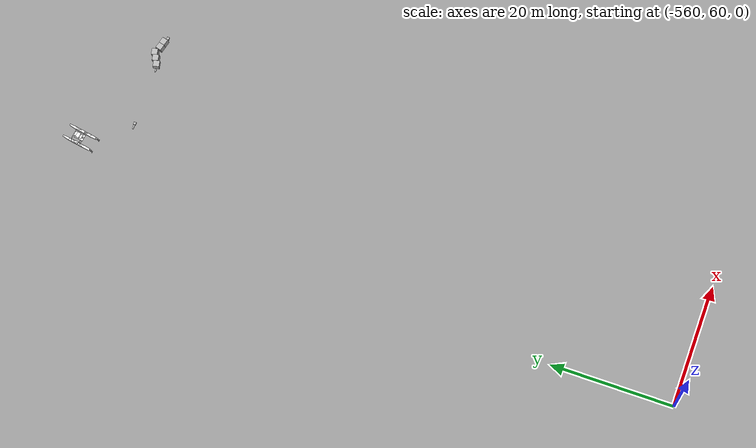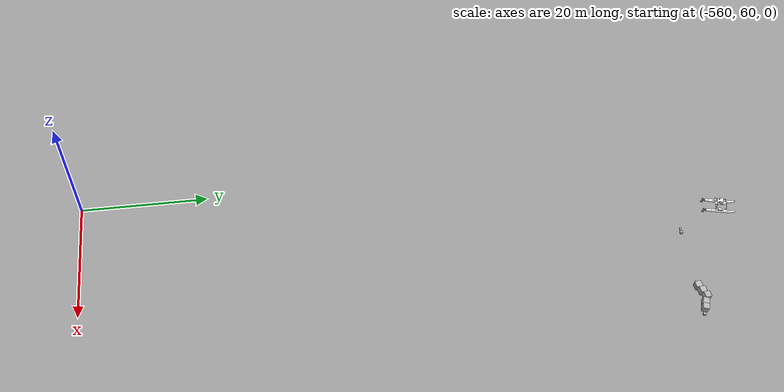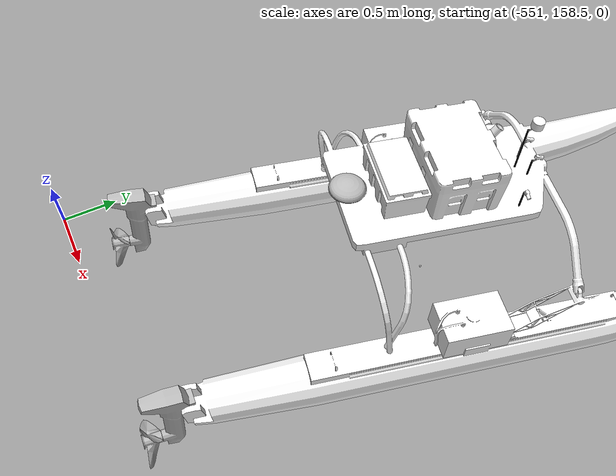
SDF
<sdf version="1.10">
 <world name="sydney_regatta">
  <physics name="4ms" type="dart">
   <max_step_size>0.0040000000000000001</max_step_size>
   <real_time_factor>1</real_time_factor>
   <real_time_update_rate>1000</real_time_update_rate>
  </physics>
  <plugin name="gz::sim::systems::Physics" filename="gz-sim-physics-system"/>
  <plugin name="gz::sim::systems::UserCommands" filename="gz-sim-user-commands-system"/>
  <plugin name="gz::sim::systems::Sensors" filename="gz-sim-sensors-system">
   <render_engine>ogre2</render_engine>
   <disable_on_drained_battery>true</disable_on_drained_battery>
  </plugin>
  <plugin name="gz::sim::systems::Imu" filename="gz-sim-imu-system"/>
  <plugin name="gz::sim::systems::Magnetometer" filename="gz-sim-magnetometer-system"/>
  <plugin name="gz::sim::systems::ForceTorque" filename="gz-sim-forcetorque-system"/>
  <plugin name="gz::sim::systems::ParticleEmitter2" filename="gz-sim-particle-emitter2-system"/>
  <plugin name="gz::sim::systems::SceneBroadcaster" filename="gz-sim-scene-broadcaster-system"/>
  <plugin name="gz::sim::systems::Contact" filename="gz-sim-contact-system"/>
  <plugin name="gz::sim::systems::NavSat" filename="gz-sim-navsat-system"/>
  <scene>
   <grid>false</grid>
   <ambient>1 1 1 1</ambient>
   <background>0.800000012 0.800000012 0.800000012 1</background>
   <shadows>true</shadows>
  </scene>
  <spherical_coordinates>
   <surface_model>EARTH_WGS84</surface_model>
   <world_frame_orientation>ENU</world_frame_orientation>
   <latitude_deg>-33.724223000000002</latitude_deg>
   <longitude_deg>150.67973599999999</longitude_deg>
   <elevation>0</elevation>
   <heading_deg>0</heading_deg>
  </spherical_coordinates>
  <plugin name="vrx::USVWind" filename="libUSVWind.so">
   <wind_obj>
    <name>wamv</name>
    <link_name>wamv/base_link</link_name>
    <coeff_vector>.5 .5 .33</coeff_vector>
   </wind_obj>
   <wind_direction>240</wind_direction>
   <wind_mean_velocity>0</wind_mean_velocity>
   <var_wind_gain_constants>0</var_wind_gain_constants>
   <var_wind_time_constants>2</var_wind_time_constants>
   <random_seed>10</random_seed>
   <update_rate>10</update_rate>
   <topic_wind_speed>/vrx/debug/wind/speed</topic_wind_speed>
   <topic_wind_direction>/vrx/debug/wind/direction</topic_wind_direction>
  </plugin>
  <plugin name="vrx::PublisherPlugin" filename="libPublisherPlugin.so">
   <message type="gz.msgs.Param" topic="/vrx/wavefield/parameters" every="2.0">params { key: "direction" value { type: DOUBLE double_value: 0.0 } } params { key: "gain" value { type: DOUBLE double_value: 3.0 } } params { key: "period" value { type: DOUBLE double_value: 5 } } params { key: "steepness" value { type: DOUBLE double_value: 0 } }</message>
  </plugin>
  <gravity>0 0 -9.8000000000000007</gravity>
  <magnetic_field>5.5644999999999998e-06 2.2875799999999999e-05 -4.2388400000000002e-05</magnetic_field>
  <atmosphere type="adiabatic"/>
  <include>
   <uri>https://fuel.gazebosim.org/1.0/openrobotics/models/post</uri>
   <name>post_0</name>
   <pose>-530 154 0.5 0 0 0</pose>
  </include>
  <include>
   <uri>https://fuel.gazebosim.org/1.0/openrobotics/models/post</uri>
   <name>post_1</name>
   <pose>-535 154 0.5 0 0 0</pose>
  </include>
  <include>
   <uri>https://fuel.gazebosim.org/1.0/openrobotics/models/post</uri>
   <name>post_2</name>
   <pose>-545 154 0.5 0 0 0</pose>
  </include>
  <include>
   <uri>file:///home/koki-22/ac_search/vrx_ws/install/share/vrx_gazebo/models/blue_projectile</uri>
   <name>blue_projectile</name>
   <pose>-545 60 -0.30119933793268233 0 0 0</pose>
  </include>
  <model name="wamv">
   <link name="wamv/base_link">
    <inertial>
     <pose>-0.0035136061477780219 -0.00096544672795737289 0.25520552255993267 0 0 0</pose>
     <mass>250.18469999999999</mass>
     <inertia>
      <ixx>225.17117280344749</ixx>
      <ixy>0.1216186764289343</ixy>
      <ixz>0.99186607687258233</ixz>
      <iyy>454.14101743117533</iyy>
      <iyz>0.29216251726199038</iyz>
      <izz>499.75243467760379</izz>
     </inertia>
    </inertial>
    <collision name="wamv/base_link_fixed_joint_lump__left_float_collision">
     <pose>-0.40000000000000002 1.03 0.20000000000000001 0 1.5707963267948966 0</pose>
     <geometry><cylinder><length>4</length><radius>0.20000000000000001</radius></cylinder></geometry>
    </collision>
    <collision name="wamv/base_link_fixed_joint_lump__left_mid_float_collision_1">
     <pose>1.8500000000000001 1.03 0.29999999999999999 0 1.3799999999999997 0</pose>
     <geometry><cylinder><length>0.5</length><radius>0.17000000000000001</radius></cylinder></geometry>
    </collision>
    <collision name="wamv/base_link_fixed_joint_lump__left_front_float_collision_2">
     <pose>2.2999999999999998 1.03 0.40000000000000002 0 1.3 0</pose>
     <geometry><cylinder><length>0.45000000000000001</length><radius>0.12</radius></cylinder></geometry>
    </collision>
    <collision name="wamv/base_link_fixed_joint_lump__front_left_beam_lower_collision_3">
     <pose>0.90000000000000002 0.84999999999999998 1 0.78000000000000003 0 0</pose>
     <geometry><cylinder><length>0.5</length><radius>0.040000000000000001</radius></cylinder></geometry>
    </collision>
    <collision name="wamv/base_link_fixed_joint_lump__front_left_beam_upper_collision_4">
     <pose>0.90000000000000002 0.59999999999999998 1.1799999999999999 1.3500000000000001 0 0</pose>
     <geometry>
      <cylinder><length>0.20000000000000001</length><radius>0.040000000000000001</radius></cylinder>
     </geometry>
    </collision>
    <collision name="wamv/base_link_fixed_joint_lump__mid_left_beam_lower_collision_5">
     <pose>-0.65000000000000002 0.98999999999999999 0.69999999999999996 0.099999999999999964 0.25000000000000011 0</pose>
     <geometry>
      <cylinder><length>0.45000000000000001</length><radius>0.029999999999999999</radius></cylinder>
     </geometry>
    </collision>
    <collision name="wamv/base_link_fixed_joint_lump__mid_left_beam_medium_collision_6">
     <pose>-0.56999999999999995 0.87 1.05 0.75000000000000056 0.25000000000000028 0</pose>
     <geometry>
      <cylinder><length>0.32000000000000001</length><radius>0.029999999999999999</radius></cylinder>
     </geometry>
    </collision>
    <collision name="wamv/base_link_fixed_joint_lump__mid_left_beam_upper_collision_7">
     <pose>-0.55000000000000004 0.65000000000000002 1.1699999999999999 1.3500000000000001 0.25000000000000011 0</pose>
     <geometry>
      <cylinder><length>0.29999999999999999</length><radius>0.029999999999999999</radius></cylinder>
     </geometry>
    </collision>
    <collision name="wamv/base_link_fixed_joint_lump__rear_left_beam_lower_collision_8">
     <pose>-0.73999999999999999 1.03 0.69999999999999996 0 -0.14999999999999999 0</pose>
     <geometry>
      <cylinder><length>0.45000000000000001</length><radius>0.029999999999999999</radius></cylinder>
     </geometry>
    </collision>
    <collision name="wamv/base_link_fixed_joint_lump__rear_left_beam_medium_collision_9">
     <pose>-0.79000000000000004 0.91000000000000003 1.05 0.75000000000000033 -0.14999999999999999 -2.1053085164236764e-17</pose>
     <geometry>
      <cylinder><length>0.32000000000000001</length><radius>0.029999999999999999</radius></cylinder>
     </geometry>
    </collision>
    <collision name="wamv/base_link_fixed_joint_lump__rear_left_beam_upper_collision_10">
     <pose>-0.81000000000000005 0.67000000000000004 1.1799999999999999 1.45 -0.14999999999999999 0</pose>
     <geometry>
      <cylinder><length>0.29999999999999999</length><radius>0.029999999999999999</radius></cylinder>
     </geometry>
    </collision>
    <collision name="wamv/base_link_fixed_joint_lump__left_joint_collision_11">
     <pose>0.57999999999999996 1.03 0.59999999999999998 0 -0.59999999999999987 0</pose>
     <geometry><box><size>0.65000000000000002 0.20000000000000001 0.10000000000000001</size></box></geometry>
    </collision>
    <collision name="wamv/base_link_fixed_joint_lump__right_float_collision_12">
     <pose>-0.40000000000000002 -1.03 0.20000000000000001 0 1.5707963267948966 0</pose>
     <geometry><cylinder><length>4</length><radius>0.20000000000000001</radius></cylinder></geometry>
    </collision>
    <collision name="wamv/base_link_fixed_joint_lump__right_mid_float_collision_13">
     <pose>1.8500000000000001 -1.03 0.29999999999999999 0 1.3799999999999997 0</pose>
     <geometry><cylinder><length>0.5</length><radius>0.17000000000000001</radius></cylinder></geometry>
    </collision>
    <collision name="wamv/base_link_fixed_joint_lump__right_front_float_collision_14">
     <pose>2.2999999999999998 -1.03 0.40000000000000002 0 1.3 0</pose>
     <geometry><cylinder><length>0.45000000000000001</length><radius>0.12</radius></cylinder></geometry>
    </collision>
    <collision name="wamv/base_link_fixed_joint_lump__front_right_beam_lower_collision_15">
     <pose>0.90000000000000002 -0.84999999999999998 1 -0.78000000000000003 0 0</pose>
     <geometry><cylinder><length>0.5</length><radius>0.040000000000000001</radius></cylinder></geometry>
    </collision>
    <collision name="wamv/base_link_fixed_joint_lump__front_right_beam_upper_collision_16">
     <pose>0.90000000000000002 -0.59999999999999998 1.1799999999999999 -1.3500000000000001 0 0</pose>
     <geometry>
      <cylinder><length>0.20000000000000001</length><radius>0.040000000000000001</radius></cylinder>
     </geometry>
    </collision>
    <collision name="wamv/base_link_fixed_joint_lump__mid_right_beam_lower_collision_17">
     <pose>-0.65000000000000002 -0.98999999999999999 0.69999999999999996 -0.099999999999999964 0.25000000000000011 0</pose>
     <geometry>
      <cylinder><length>0.45000000000000001</length><radius>0.029999999999999999</radius></cylinder>
     </geometry>
    </collision>
    <collision name="wamv/base_link_fixed_joint_lump__mid_right_beam_medium_collision_18">
     <pose>-0.56999999999999995 -0.87 1.05 -0.75000000000000056 0.25000000000000028 0</pose>
     <geometry>
      <cylinder><length>0.32000000000000001</length><radius>0.029999999999999999</radius></cylinder>
     </geometry>
    </collision>
    <collision name="wamv/base_link_fixed_joint_lump__mid_right_beam_upper_collision_19">
     <pose>-0.55000000000000004 -0.65000000000000002 1.1699999999999999 -1.3500000000000001 0.25000000000000011 0</pose>
     <geometry>
      <cylinder><length>0.29999999999999999</length><radius>0.029999999999999999</radius></cylinder>
     </geometry>
    </collision>
    <collision name="wamv/base_link_fixed_joint_lump__rear_right_beam_lower_collision_20">
     <pose>-0.73999999999999999 -1.03 0.69999999999999996 0 -0.14999999999999999 0</pose>
     <geometry>
      <cylinder><length>0.45000000000000001</length><radius>0.029999999999999999</radius></cylinder>
     </geometry>
    </collision>
    <collision name="wamv/base_link_fixed_joint_lump__rear_right_beam_medium_collision_21">
     <pose>-0.79000000000000004 -0.91000000000000003 1.05 -0.75000000000000033 -0.14999999999999999 2.1053085164236764e-17</pose>
     <geometry>
      <cylinder><length>0.32000000000000001</length><radius>0.029999999999999999</radius></cylinder>
     </geometry>
    </collision>
    <collision name="wamv/base_link_fixed_joint_lump__rear_right_beam_upper_collision_22">
     <pose>-0.81000000000000005 -0.67000000000000004 1.1799999999999999 -1.45 -0.14999999999999999 0</pose>
     <geometry>
      <cylinder><length>0.29999999999999999</length><radius>0.029999999999999999</radius></cylinder>
     </geometry>
    </collision>
    <collision name="wamv/base_link_fixed_joint_lump__right_joint_collision_23">
     <pose>0.57999999999999996 -1.03 0.59999999999999998 0 -0.59999999999999987 0</pose>
     <geometry><box><size>0.65000000000000002 0.20000000000000001 0.10000000000000001</size></box></geometry>
    </collision>
    <collision name="wamv/base_link_fixed_joint_lump__top_base_collision_24">
     <pose>0 0 1.25 0 0 0</pose>
     <geometry><box><size>1.8500000000000001 1 0.10000000000000001</size></box></geometry>
    </collision>
    <collision name="wamv/base_link_fixed_joint_lump__front_left_camera_post_collision_collision_25">
     <pose>0.69999999999999996 0.10000000000000001 1.3847499999999999 0 0 0</pose>
     <geometry><cylinder><length>0.17649999999999999</length><radius>0.0076</radius></cylinder></geometry>
    </collision>
    <collision name="wamv/base_link_fixed_joint_lump__front_left_camera_post_arm_collision_collision_26">
     <pose>0.72999999999999998 0.10000000000000001 1.4730000000000001 -1.2042771838760871 5.5511151231257827e-17 -1.570796326794897</pose>
     <geometry>
      <cylinder><length>0.065000000000000002</length><radius>0.0080000000000000002</radius></cylinder>
     </geometry>
    </collision>
    <collision name="wamv/base_link_fixed_joint_lump__front_left_camera_lens_collision_collision_27">
     <pose>0.76738666487320317 0.10000000000000001 1.495341257188155 3.1415926535897931 1.3089969389957472 3.1415926535897931</pose>
     <geometry>
      <cylinder><length>0.042000000000000003</length><radius>0.014999999999999999</radius></cylinder>
     </geometry>
    </collision>
    <collision name="wamv/base_link_fixed_joint_lump__front_left_camera_box_collision_collision_28">
     <pose>0.73019852056107404 0.10000000000000001 1.5053057904246021 0 0.26179938779914941 0</pose>
     <geometry><box><size>0.035999999999999997 0.029999999999999999 0.029999999999999999</size></box></geometry>
    </collision>
    <collision name="wamv/base_link_fixed_joint_lump__front_right_camera_post_collision_collision_29">
     <pose>0.69999999999999996 -0.10000000000000001 1.3847499999999999 0 0 0</pose>
     <geometry><cylinder><length>0.17649999999999999</length><radius>0.0076</radius></cylinder></geometry>
    </collision>
    <collision name="wamv/base_link_fixed_joint_lump__front_right_camera_post_arm_collision_collision_30">
     <pose>0.72999999999999998 -0.10000000000000001 1.4730000000000001 -1.2042771838760871 5.5511151231257827e-17 -1.570796326794897</pose>
     <geometry>
      <cylinder><length>0.065000000000000002</length><radius>0.0080000000000000002</radius></cylinder>
     </geometry>
    </collision>
    <collision name="wamv/base_link_fixed_joint_lump__front_right_camera_lens_collision_collision_31">
     <pose>0.76738666487320317 -0.10000000000000001 1.495341257188155 3.1415926535897931 1.3089969389957472 3.1415926535897931</pose>
     <geometry>
      <cylinder><length>0.042000000000000003</length><radius>0.014999999999999999</radius></cylinder>
     </geometry>
    </collision>
    <collision name="wamv/base_link_fixed_joint_lump__front_right_camera_box_collision_collision_32">
     <pose>0.73019852056107404 -0.10000000000000001 1.5053057904246021 0 0.26179938779914941 0</pose>
     <geometry><box><size>0.035999999999999997 0.029999999999999999 0.029999999999999999</size></box></geometry>
    </collision>
    <collision name="wamv/base_link_fixed_joint_lump__lidar_wamv_post_collision_collision_33">
     <pose>0.62999999999999989 0 1.52325 0 0 0</pose>
     <geometry><cylinder><length>0.45350000000000013</length><radius>0.0076</radius></cylinder></geometry>
    </collision>
    <collision name="wamv/base_link_fixed_joint_lump__lidar_wamv_post_arm_collision_collision_34">
     <pose>0.65999999999999992 0 1.75 -1.2042771838760871 5.5511151231257827e-17 -1.570796326794897</pose>
     <geometry>
      <cylinder><length>0.065000000000000002</length><radius>0.0080000000000000002</radius></cylinder>
     </geometry>
    </collision>
    <collision name="wamv/base_link_fixed_joint_lump__lidar_wamv_collision_collision_35">
     <pose>0.69999999999999996 0 1.8 0 0 0</pose>
     <geometry><cylinder><length>0.074999999999999997</length><radius>0.055</radius></cylinder></geometry>
    </collision>
    <collision name="wamv/base_link_fixed_joint_lump__middle_right_camera_post_collision_collision_36">
     <pose>0.5 -0.40000000000000002 1.3847499999999999 0 0 -1.5707963267948959</pose>
     <geometry><cylinder><length>0.17649999999999999</length><radius>0.0076</radius></cylinder></geometry>
    </collision>
    <collision name="wamv/base_link_fixed_joint_lump__middle_right_camera_post_arm_collision_collision_37">
     <pose>0.5 -0.42999999999999999 1.4730000000000001 -1.2042771838760871 -5.7225324855899147e-17 -3.1415926535897931</pose>
     <geometry>
      <cylinder><length>0.065000000000000002</length><radius>0.0080000000000000002</radius></cylinder>
     </geometry>
    </collision>
    <collision name="wamv/base_link_fixed_joint_lump__middle_right_camera_lens_collision_collision_38">
     <pose>0.5 -0.46738666487320318 1.495341257188155 3.1415926535897927 1.3089969389957476 1.5707963267948957</pose>
     <geometry>
      <cylinder><length>0.042000000000000003</length><radius>0.014999999999999999</radius></cylinder>
     </geometry>
    </collision>
    <collision name="wamv/base_link_fixed_joint_lump__middle_right_camera_box_collision_collision_39">
     <pose>0.5 -0.4301985205610741 1.5053057904246021 0 0.26179938779914952 -1.570796326794897</pose>
     <geometry><box><size>0.035999999999999997 0.029999999999999999 0.029999999999999999</size></box></geometry>
    </collision>
    <collision name="wamv/base_link_fixed_joint_lump__cpu_case_1_collision_collision_40">
     <pose>0.035000000000000003 0 1.53 0 0 0</pose>
     <geometry><box><size>0.59499999999999997 0.82999999999999996 0.46999999999999997</size></box></geometry>
    </collision>
    <collision name="wamv/base_link_fixed_joint_lump__cpu_case_2_collision_collision_41">
     <pose>-0.45000000000000001 0 1.4379999999999999 0 0 0</pose>
     <geometry><box><size>0.375 0.64000000000000001 0.28000000000000003</size></box></geometry>
    </collision>
    <collision name="wamv/base_link_fixed_joint_lump__left_battery_collision_collision_42">
     <pose>0 1 0.59999999999999998 0 0 0</pose>
     <geometry><box><size>0.59999999999999998 0.40000000000000002 0.31</size></box></geometry>
    </collision>
    <collision name="wamv/base_link_fixed_joint_lump__right_battery_collision_collision_43">
     <pose>0 -1 0.59999999999999998 0 0 0</pose>
     <geometry><box><size>0.59999999999999998 0.40000000000000002 0.31</size></box></geometry>
    </collision>
    <visual name="wamv/base_link_visual">
     <geometry>
      <mesh>
       <scale>1 1 1</scale>
       <uri>file:///model://wamv_description/models/WAM-V-Base/mesh/WAM-V-Base.dae</uri>
      </mesh>
     </geometry>
     <material>
      <diffuse>1 1 1 1</diffuse>
      <specular>1 1 1 1</specular>
      <pbr>
       <metal>
        <albedo_map>model://wamv_description/models/WAM-V-Base/mesh/WAM-V_Albedo.png</albedo_map>
        <normal_map>model://wamv_description/models/WAM-V-Base/mesh/WAM-V_Normal.png</normal_map>
        <roughness_map>model://wamv_description/models/WAM-V-Base/mesh/WAM-V_Roughness.png</roughness_map>
        <metalness_map>model://wamv_description/models/WAM-V-Base/mesh/WAM-V_Metalness.png</metalness_map>
       </metal>
      </pbr>
     </material>
    </visual>
    <visual name="wamv/base_link_fixed_joint_lump__wamv/front_left_camera_post_link_visual_1">
     <pose>0.69999999999999996 0.10000000000000001 1.3847499999999999 0 0 0</pose>
     <geometry><cylinder><length>0.17649999999999999</length><radius>0.0076</radius></cylinder></geometry>
     <material><diffuse>0 0 0 1</diffuse><ambient>0 0 0 1</ambient></material>
    </visual>
    <visual name="wamv/base_link_fixed_joint_lump__front_left_camera_post_arm_visual_visual_2">
     <pose>0.69199999999999995 0.10000000000000001 1.47 -1.0471975511965981 5.5511151231257827e-17 -1.570796326794897</pose>
     <geometry>
      <mesh>
       <scale>1 1 1</scale>
       <uri>file:///model://vrx_gazebo/models/sensor_post/mesh/sensor_post_arm.dae</uri>
      </mesh>
     </geometry>
    </visual>
    <visual name="wamv/base_link_fixed_joint_lump__wamv/front_left_camera_link_visual_3">
     <pose>0.71812444773246065 0.10000000000000001 1.5085410284883829 0.26179938779914941 2.7755575615628914e-17 1.570796326794897</pose>
     <geometry>
      <mesh><scale>1 1 1</scale><uri>file:///model://vrx_gazebo/models/mono_camera/mesh/mono_camera.dae</uri></mesh>
     </geometry>
     <material>
      <diffuse>1 1 1 1</diffuse>
      <specular>1 1 1 1</specular>
      <pbr>
       <metal>
        <albedo_map>model://vrx_gazebo/models/mono_camera/mesh/mono_camera_Albedo.png</albedo_map>
        <normal_map>model://vrx_gazebo/models/mono_camera/mesh/mono_camera_Normal.png</normal_map>
        <roughness_map>model://vrx_gazebo/models/mono_camera/mesh/mono_camera_Roughness.png</roughness_map>
        <metalness_map>model://vrx_gazebo/models/mono_camera/mesh/mono_camera_Metalness.png</metalness_map>
       </metal>
      </pbr>
     </material>
    </visual>
    <visual name="wamv/base_link_fixed_joint_lump__wamv/front_right_camera_post_link_visual_4">
     <pose>0.69999999999999996 -0.10000000000000001 1.3847499999999999 0 0 0</pose>
     <geometry><cylinder><length>0.17649999999999999</length><radius>0.0076</radius></cylinder></geometry>
     <material><diffuse>0 0 0 1</diffuse><ambient>0 0 0 1</ambient></material>
    </visual>
    <visual name="wamv/base_link_fixed_joint_lump__front_right_camera_post_arm_visual_visual_5">
     <pose>0.69199999999999995 -0.10000000000000001 1.47 -1.0471975511965981 5.5511151231257827e-17 -1.570796326794897</pose>
     <geometry>
      <mesh>
       <scale>1 1 1</scale>
       <uri>file:///model://vrx_gazebo/models/sensor_post/mesh/sensor_post_arm.dae</uri>
      </mesh>
     </geometry>
    </visual>
    <visual name="wamv/base_link_fixed_joint_lump__wamv/front_right_camera_link_visual_6">
     <pose>0.71812444773246065 -0.10000000000000001 1.5085410284883829 0.26179938779914941 2.7755575615628914e-17 1.570796326794897</pose>
     <geometry>
      <mesh><scale>1 1 1</scale><uri>file:///model://vrx_gazebo/models/mono_camera/mesh/mono_camera.dae</uri></mesh>
     </geometry>
     <material>
      <diffuse>1 1 1 1</diffuse>
      <specular>1 1 1 1</specular>
      <pbr>
       <metal>
        <albedo_map>model://vrx_gazebo/models/mono_camera/mesh/mono_camera_Albedo.png</albedo_map>
        <normal_map>model://vrx_gazebo/models/mono_camera/mesh/mono_camera_Normal.png</normal_map>
        <roughness_map>model://vrx_gazebo/models/mono_camera/mesh/mono_camera_Roughness.png</roughness_map>
        <metalness_map>model://vrx_gazebo/models/mono_camera/mesh/mono_camera_Metalness.png</metalness_map>
       </metal>
      </pbr>
     </material>
    </visual>
    <visual name="wamv/base_link_fixed_joint_lump__wamv/lidar_wamv_post_link_visual_7">
     <pose>0.62999999999999989 0 1.52325 0 0 0</pose>
     <geometry><cylinder><length>0.45350000000000013</length><radius>0.0076</radius></cylinder></geometry>
     <material><diffuse>0 0 0 1</diffuse><ambient>0 0 0 1</ambient></material>
    </visual>
    <visual name="wamv/base_link_fixed_joint_lump__lidar_wamv_post_arm_visual_visual_8">
     <pose>0.62199999999999989 0 1.7470000000000001 -1.0471975511965981 5.5511151231257827e-17 -1.570796326794897</pose>
     <geometry>
      <mesh>
       <scale>1 1 1</scale>
       <uri>file:///model://vrx_gazebo/models/sensor_post/mesh/sensor_post_arm.dae</uri>
      </mesh>
     </geometry>
    </visual>
    <visual name="wamv/base_link_fixed_joint_lump__wamv/lidar_wamv_link_visual_9">
     <pose>0.69999999999999996 0 1.7649999999999999 0 0 0</pose>
     <geometry>
      <mesh><scale>1 1 1</scale><uri>file:///model://vrx_gazebo/models/3d_lidar/mesh/3d_lidar.dae</uri></mesh>
     </geometry>
     <material>
      <diffuse>1 1 1 1</diffuse>
      <specular>1 1 1 1</specular>
      <pbr>
       <metal>
        <albedo_map>model://vrx_gazebo/models/3d_lidar/mesh/3d_Lidar_Albedo.png</albedo_map>
        <normal_map>model://vrx_gazebo/models/3d_lidar/mesh/3d_Lidar_Normal.png</normal_map>
        <roughness_map>model://vrx_gazebo/models/3d_lidar/mesh/3d_Lidar_Roughness.png</roughness_map>
        <metalness_map>model://vrx_gazebo/models/3d_lidar/mesh/3d_Lidar_Metalness.png</metalness_map>
       </metal>
      </pbr>
     </material>
    </visual>
    <visual name="wamv/base_link_fixed_joint_lump__wamv/middle_right_camera_post_link_visual_10">
     <pose>0.5 -0.40000000000000002 1.3847499999999999 0 0 -1.5707963267948959</pose>
     <geometry><cylinder><length>0.17649999999999999</length><radius>0.0076</radius></cylinder></geometry>
     <material><diffuse>0 0 0 1</diffuse><ambient>0 0 0 1</ambient></material>
    </visual>
    <visual name="wamv/base_link_fixed_joint_lump__middle_right_camera_post_arm_visual_visual_11">
     <pose>0.5 -0.39200000000000002 1.47 -1.0471975511965981 2.2311252215006139e-17 -3.1415926535897931</pose>
     <geometry>
      <mesh>
       <scale>1 1 1</scale>
       <uri>file:///model://vrx_gazebo/models/sensor_post/mesh/sensor_post_arm.dae</uri>
      </mesh>
     </geometry>
    </visual>
    <visual name="wamv/base_link_fixed_joint_lump__wamv/middle_right_camera_link_visual_12">
     <pose>0.5 -0.41812444773246082 1.5085410284883829 0.26179938779914952 5.5036245637175027e-17 7.2456591959675132e-18</pose>
     <geometry>
      <mesh><scale>1 1 1</scale><uri>file:///model://vrx_gazebo/models/mono_camera/mesh/mono_camera.dae</uri></mesh>
     </geometry>
     <material>
      <diffuse>1 1 1 1</diffuse>
      <specular>1 1 1 1</specular>
      <pbr>
       <metal>
        <albedo_map>model://vrx_gazebo/models/mono_camera/mesh/mono_camera_Albedo.png</albedo_map>
        <normal_map>model://vrx_gazebo/models/mono_camera/mesh/mono_camera_Normal.png</normal_map>
        <roughness_map>model://vrx_gazebo/models/mono_camera/mesh/mono_camera_Roughness.png</roughness_map>
        <metalness_map>model://vrx_gazebo/models/mono_camera/mesh/mono_camera_Metalness.png</metalness_map>
       </metal>
      </pbr>
     </material>
    </visual>
    <visual name="wamv/base_link_fixed_joint_lump__wamv/cpu_cases_link_visual_13">
     <pose>-0.076999999999999999 0 0 0 0 0</pose>
     <geometry>
      <mesh><scale>1 1 1</scale><uri>file:///model://vrx_gazebo/models/cpu_cases/mesh/cpu_cases.dae</uri></mesh>
     </geometry>
     <material>
      <diffuse>1 1 1 1</diffuse>
      <specular>1 1 1 1</specular>
      <pbr>
       <metal>
        <albedo_map>model://vrx_gazebo/models/cpu_cases/mesh/cpu_cases_Albedo.png</albedo_map>
        <normal_map>model://vrx_gazebo/models/cpu_cases/mesh/cpu_cases_Normal.png</normal_map>
        <roughness_map>model://vrx_gazebo/models/cpu_cases/mesh/cpu_cases_Roughness.png</roughness_map>
        <metalness_map>model://vrx_gazebo/models/cpu_cases/mesh/cpu_cases_Metalness.png</metalness_map>
       </metal>
      </pbr>
     </material>
    </visual>
    <visual name="wamv/base_link_fixed_joint_lump__wamv/left_battery_link_visual_14">
     <pose>0 -0.03000000000000003 0 0 0 0</pose>
     <geometry>
      <mesh><scale>1 1 1</scale><uri>file:///model://vrx_gazebo/models/battery/mesh/battery.dae</uri></mesh>
     </geometry>
     <material>
      <diffuse>1 1 1 1</diffuse>
      <specular>1 1 1 1</specular>
      <pbr>
       <metal>
        <albedo_map>model://vrx_gazebo/models/battery/mesh/battery_Albedo.png</albedo_map>
        <normal_map>model://vrx_gazebo/models/battery/mesh/battery_Normal.png</normal_map>
        <roughness_map>model://vrx_gazebo/models/battery/mesh/battery_Roughness.png</roughness_map>
        <metalness_map>model://vrx_gazebo/models/battery/mesh/battery_Metalness.png</metalness_map>
       </metal>
      </pbr>
     </material>
    </visual>
    <visual name="wamv/base_link_fixed_joint_lump__wamv/right_battery_link_visual_15">
     <pose>0 -2.0299999999999998 0 0 0 0</pose>
     <geometry>
      <mesh><scale>1 1 1</scale><uri>file:///model://vrx_gazebo/models/battery/mesh/battery.dae</uri></mesh>
     </geometry>
     <material>
      <diffuse>1 1 1 1</diffuse>
      <specular>1 1 1 1</specular>
      <pbr>
       <metal>
        <albedo_map>model://vrx_gazebo/models/battery/mesh/battery_Albedo.png</albedo_map>
        <normal_map>model://vrx_gazebo/models/battery/mesh/battery_Normal.png</normal_map>
        <roughness_map>model://vrx_gazebo/models/battery/mesh/battery_Roughness.png</roughness_map>
        <metalness_map>model://vrx_gazebo/models/battery/mesh/battery_Metalness.png</metalness_map>
       </metal>
      </pbr>
     </material>
    </visual>
    <sensor name="contact_sensor" type="contact">
     <contact>
      <collision>wamv/base_link_fixed_joint_lump__top_base_collision_24</collision>
      <collision>wamv/base_link_fixed_joint_lump__left_float_collision</collision>
      <collision>wamv/base_link_fixed_joint_lump__left_mid_float_collision_1</collision>
      <collision>wamv/base_link_fixed_joint_lump__left_front_float_collision_2</collision>
      <collision>wamv/base_link_fixed_joint_lump__right_float_collision_12</collision>
      <collision>wamv/base_link_fixed_joint_lump__right_mid_float_collision_13</collision>
      <collision>wamv/base_link_fixed_joint_lump__right_front_float_collision_14</collision>
      <topic>/vrx/contacts</topic>
     </contact>
     <always_on>true</always_on>
     <update_rate>5</update_rate>
    </sensor>
    <sensor name="front_left_camera_sensor" type="camera">
     <pose>0.75 0.10000000000000001 1.5 0 0.261799 0</pose>
     <topic>__default__</topic>
     <update_rate>30</update_rate>
     <enable_metrics>false</enable_metrics>
     <camera name="front_left_camera_camera">
      <horizontal_fov>1.3962634</horizontal_fov>
      <image>
       <width>1280</width>
       <height>720</height>
       <format>RGB_INT8</format>
       <anti_aliasing>4</anti_aliasing>
      </image>
      <camera_info_topic>__default__</camera_info_topic>
      <triggered>false</triggered>
      <clip><near>0.050000000000000003</near><far>400</far></clip>
      <save enabled="false"><path>__default__</path></save>
      <visibility_mask>4294967295</visibility_mask>
      <noise><type>gaussian</type><mean>0</mean><stddev>0.0070000000000000001</stddev></noise>
      <distortion><k1>0</k1><k2>0</k2><k3>0</k3><p1>0</p1><p2>0</p2><center>0.5 0.5</center></distortion>
      <lens>
       <type>stereographic</type>
       <scale_to_hfov>true</scale_to_hfov>
       <cutoff_angle>1.5707963267948966</cutoff_angle>
       <env_texture_size>256</env_texture_size>
      </lens>
     </camera>
    </sensor>
    <sensor name="front_right_camera_sensor" type="camera">
     <pose>0.75 -0.10000000000000001 1.5 0 0.261799 0</pose>
     <topic>__default__</topic>
     <update_rate>30</update_rate>
     <enable_metrics>false</enable_metrics>
     <camera name="front_right_camera_camera">
      <horizontal_fov>1.3962634</horizontal_fov>
      <image>
       <width>1280</width>
       <height>720</height>
       <format>RGB_INT8</format>
       <anti_aliasing>4</anti_aliasing>
      </image>
      <camera_info_topic>__default__</camera_info_topic>
      <triggered>false</triggered>
      <clip><near>0.050000000000000003</near><far>400</far></clip>
      <save enabled="false"><path>__default__</path></save>
      <visibility_mask>4294967295</visibility_mask>
      <noise><type>gaussian</type><mean>0</mean><stddev>0.0070000000000000001</stddev></noise>
      <distortion><k1>0</k1><k2>0</k2><k3>0</k3><p1>0</p1><p2>0</p2><center>0.5 0.5</center></distortion>
      <lens>
       <type>stereographic</type>
       <scale_to_hfov>true</scale_to_hfov>
       <cutoff_angle>1.5707963267948966</cutoff_angle>
       <env_texture_size>256</env_texture_size>
      </lens>
     </camera>
    </sensor>
    <sensor name="lidar_wamv_sensor" type="gpu_lidar">
     <pose>0.69999999999999996 0 1.8 0 0 0</pose>
     <topic>__default__</topic>
     <update_rate>10</update_rate>
     <enable_metrics>false</enable_metrics>
     <lidar>
      <scan>
       <horizontal>
        <samples>1875</samples>
        <resolution>1</resolution>
        <min_angle>-3.1415926535897931</min_angle>
        <max_angle>3.1415926535897931</max_angle>
       </horizontal>
       <vertical>
        <samples>16</samples>
        <min_angle>-0.26179938779914941</min_angle>
        <max_angle>0.26179938779914941</max_angle>
        <resolution>1</resolution>
       </vertical>
      </scan>
      <range><min>0.10000000000000001</min><max>130</max><resolution>0</resolution></range>
      <noise><type>gaussian</type><mean>0</mean><stddev>0.01</stddev></noise>
      <visibility_mask>4294967295</visibility_mask>
     </lidar>
    </sensor>
    <sensor name="middle_right_camera_sensor" type="camera">
     <pose>0.5 -0.45000000000000001 1.5 -2.873468332259928e-17 0.261799 -1.5708</pose>
     <topic>__default__</topic>
     <update_rate>30</update_rate>
     <enable_metrics>false</enable_metrics>
     <camera name="middle_right_camera_camera">
      <horizontal_fov>1.3962634</horizontal_fov>
      <image>
       <width>1280</width>
       <height>720</height>
       <format>RGB_INT8</format>
       <anti_aliasing>4</anti_aliasing>
      </image>
      <camera_info_topic>__default__</camera_info_topic>
      <triggered>false</triggered>
      <clip><near>0.050000000000000003</near><far>400</far></clip>
      <save enabled="false"><path>__default__</path></save>
      <visibility_mask>4294967295</visibility_mask>
      <noise><type>gaussian</type><mean>0</mean><stddev>0.0070000000000000001</stddev></noise>
      <distortion><k1>0</k1><k2>0</k2><k3>0</k3><p1>0</p1><p2>0</p2><center>0.5 0.5</center></distortion>
      <lens>
       <type>stereographic</type>
       <scale_to_hfov>true</scale_to_hfov>
       <cutoff_angle>1.5707963267948966</cutoff_angle>
       <env_texture_size>256</env_texture_size>
      </lens>
     </camera>
    </sensor>
    <enable_wind>true</enable_wind>
   </link>
   <joint name="wamv/ball_shooter_base_joint" type="revolute">
    <parent>wamv/base_link</parent>
    <child>wamv/ball_shooter_base_link</child>
    <axis>
     <xyz>0 0 1</xyz>
     <limit>
      <lower>0</lower>
      <upper>0</upper>
      <effort>1000</effort>
      <velocity>0</velocity>
      <stiffness>100000000</stiffness>
      <dissipation>1</dissipation>
     </limit>
     <dynamics>
      <spring_reference>0</spring_reference>
      <spring_stiffness>0</spring_stiffness>
      <damping>0</damping>
      <friction>0</friction>
     </dynamics>
    </axis>
   </joint>
   <link name="wamv/ball_shooter_base_link">
    <pose>0.53999999999999204 0.3000000000001819 1.2959999999999923 2.7647152241045209e-18 1.3212973240362016e-21 -0.00095582880429823287</pose>
    <inertial>
     <pose>-0.02 0 0.050000000000000003 0 0 0</pose>
     <mass>0.5</mass>
     <inertia>
      <ixx>0.00083000000000000001</ixx>
      <ixy>0</ixy>
      <ixz>0</ixz>
      <iyy>0.00052083000000000001</iyy>
      <iyz>0</iyz>
      <izz>0.00052083000000000001</izz>
     </inertia>
    </inertial>
    <visual name="wamv/ball_shooter_base_link_visual">
     <geometry>
      <mesh>
       <scale>1 1 1</scale>
       <uri>file:///model://vrx_gazebo/models/ball_shooter/meshes/ball_shooter_base.dae</uri>
      </mesh>
     </geometry>
     <material>
      <diffuse>1 1 1 1</diffuse>
      <specular>1 1 1 1</specular>
      <pbr>
       <metal>
        <albedo_map>model://vrx_gazebo/models/ball_shooter/materials/Textures/Launcher_Albedo.png</albedo_map>
        <normal_map>model://vrx_gazebo/models/ball_shooter/materials/Textures/Launcher_Normal.png</normal_map>
        <roughness_map>model://vrx_gazebo/models/ball_shooter/materials/Textures/Launcher_Roughness.png</roughness_map>
        <metalness_map>model://vrx_gazebo/models/ball_shooter/materials/Textures/Launcher_Metalness.png</metalness_map>
       </metal>
      </pbr>
     </material>
    </visual>
    <enable_wind>true</enable_wind>
   </link>
   <joint name="wamv/ball_shooter_launcher_joint" type="revolute">
    <pose>0 0 -1.1102230246251565e-16 0 0 0</pose>
    <parent>wamv/ball_shooter_base_link</parent>
    <child>wamv/ball_shooter_launcher_link</child>
    <axis>
     <xyz>0 0 1</xyz>
     <limit>
      <lower>0</lower>
      <upper>0</upper>
      <effort>1000</effort>
      <velocity>0</velocity>
      <stiffness>100000000</stiffness>
      <dissipation>1</dissipation>
     </limit>
     <dynamics>
      <spring_reference>0</spring_reference>
      <spring_stiffness>0</spring_stiffness>
      <damping>0</damping>
      <friction>0</friction>
     </dynamics>
    </axis>
   </joint>
   <link name="wamv/ball_shooter_launcher_link">
    <pose>0.51960000931873651 0.30001949890470314 1.4038770000000014 -9.3355104466261219e-07 -1.039999999999744 -0.00095474630607414565</pose>
    <inertial>
     <pose>0 0 0 3.1415926535897931 -1.5707926536359933 3.1415926535897931</pose>
     <mass>0.5</mass>
     <inertia>
      <ixx>0.0017791669999999999</ixx>
      <ixy>0</ixy>
      <ixz>0</ixz>
      <iyy>0.0017791669999999999</iyy>
      <iyz>0</iyz>
      <izz>0.00022499999999999999</izz>
     </inertia>
    </inertial>
    <collision name="wamv/ball_shooter_launcher_link_fixed_joint_lump__ball_shooter_collision_collision">
     <pose>0 0 0 0 0.261799 0</pose>
     <geometry><box><size>0.29999999999999999 0.29999999999999999 0.20000000000000001</size></box></geometry>
    </collision>
    <visual name="wamv/ball_shooter_launcher_link_visual">
     <pose>0 0 0 0 0.261799 0</pose>
     <geometry>
      <mesh>
       <scale>1 1 1</scale>
       <uri>file:///model://vrx_gazebo/models/ball_shooter/meshes/ball_shooter_launcher.dae</uri>
      </mesh>
     </geometry>
     <material>
      <diffuse>1 1 1 1</diffuse>
      <specular>1 1 1 1</specular>
      <pbr>
       <metal>
        <albedo_map>model://vrx_gazebo/models/ball_shooter/materials/Textures/Launcher_Albedo.png</albedo_map>
        <normal_map>model://vrx_gazebo/models/ball_shooter/materials/Textures/Launcher_Normal.png</normal_map>
        <roughness_map>model://vrx_gazebo/models/ball_shooter/materials/Textures/Launcher_Roughness.png</roughness_map>
        <metalness_map>model://vrx_gazebo/models/ball_shooter/materials/Textures/Launcher_Metalness.png</metalness_map>
       </metal>
      </pbr>
     </material>
    </visual>
    <enable_wind>true</enable_wind>
   </link>
   <joint name="wamv/gps_wamv_joint" type="revolute">
    <parent>wamv/base_link</parent>
    <child>wamv/gps_wamv_link</child>
    <axis>
     <xyz>0 0 1</xyz>
     <limit>
      <lower>0</lower>
      <upper>0</upper>
      <effort>1000</effort>
      <velocity>0</velocity>
      <stiffness>100000000</stiffness>
      <dissipation>1</dissipation>
     </limit>
     <dynamics>
      <spring_reference>0</spring_reference>
      <spring_stiffness>0</spring_stiffness>
      <damping>0</damping>
      <friction>0</friction>
     </dynamics>
    </axis>
   </joint>
   <link name="wamv/gps_wamv_link">
    <pose>-0.84999999999999432 1.1368683772161603e-13 1.2999999999999972 1.4203048340922697e-17 -6.9388941467431698e-18 3.4194904352524709e-08</pose>
    <inertial>
     <mass>1</mass>
     <inertia>
      <ixx>0.0064580000000000002</ixx>
      <ixy>0</ixy>
      <ixz>0</ixz>
      <iyy>0.0064580000000000002</iyy>
      <iyz>0</iyz>
      <izz>0.01125</izz>
     </inertia>
    </inertial>
    <collision name="wamv/gps_wamv_link_fixed_joint_lump__gps_wamv_collision_base_collision">
     <pose>0 0 0.025000000000000001 0 0 0</pose>
     <geometry>
      <cylinder><length>0.050000000000000003</length><radius>0.014999999999999999</radius></cylinder>
     </geometry>
    </collision>
    <collision name="wamv/gps_wamv_link_fixed_joint_lump__gps_wamv_collision_antenna_collision_1">
     <pose>0 0 0.11 0 0 0</pose>
     <geometry>
      <cylinder><length>0.10000000000000001</length><radius>0.14999999999999999</radius></cylinder>
     </geometry>
    </collision>
    <visual name="wamv/gps_wamv_link_fixed_joint_lump__gps_wamv_visual_visual">
     <geometry>
      <mesh><scale>1 1 1</scale><uri>file:///model://wamv_gazebo/models/gps/mesh/gps.dae</uri></mesh>
     </geometry>
    </visual>
    <sensor name="navsat" type="navsat"><always_on>true</always_on><update_rate>20</update_rate></sensor>
    <enable_wind>true</enable_wind>
   </link>
   <joint name="wamv/imu_wamv_joint" type="revolute">
    <parent>wamv/base_link</parent>
    <child>wamv/imu_wamv_link</child>
    <axis>
     <xyz>0 0 1</xyz>
     <limit>
      <lower>0</lower>
      <upper>0</upper>
      <effort>1000</effort>
      <velocity>0</velocity>
      <stiffness>100000000</stiffness>
      <dissipation>1</dissipation>
     </limit>
     <dynamics>
      <spring_reference>0</spring_reference>
      <spring_stiffness>0</spring_stiffness>
      <damping>0</damping>
      <friction>0</friction>
     </dynamics>
    </axis>
   </joint>
   <link name="wamv/imu_wamv_link">
    <pose>0.29999999999995453 -0.20000000000004547 1.2999999999999972 5.7733765684853127e-18 -8.3473707845342378e-27 2.8916772309983693e-09</pose>
    <inertial>
     <mass>0.10000000000000001</mass>
     <inertia>
      <ixx>5.4199999999999998e-06</ixx>
      <ixy>0</ixy>
      <ixz>0</ixz>
      <iyy>2.1039999999999998e-05</iyy>
      <iyz>0</iyz>
      <izz>2.6040000000000001e-05</izz>
     </inertia>
    </inertial>
    <collision name="wamv/imu_wamv_link_fixed_joint_lump__imu_wamv_collision_collision">
     <geometry><box><size>0.050000000000000003 0.025000000000000001 0.0050000000000000001</size></box></geometry>
    </collision>
    <visual name="wamv/imu_wamv_link_fixed_joint_lump__imu_wamv_visual_visual">
     <geometry><box><size>0.050000000000000003 0.025000000000000001 0.0050000000000000001</size></box></geometry>
     <material><diffuse>1 0 0 1</diffuse><ambient>1 0 0 1</ambient></material>
    </visual>
    <sensor name="imu_wamv_sensor" type="imu">
     <topic>__default__</topic>
     <update_rate>100</update_rate>
     <enable_metrics>false</enable_metrics>
     <imu>
      <orientation_reference_frame>
       <localization>ENU</localization>
       <custom_rpy>0 0 0</custom_rpy>
       <grav_dir_x>1 0 0</grav_dir_x>
      </orientation_reference_frame>
      <angular_velocity>
       <x>
        <noise type="gaussian">
         <mean>0</mean>
         <stddev>0.0089999999999999993</stddev>
         <bias_mean>0.00075000000000000002</bias_mean>
         <bias_stddev>0.0050000000000000001</bias_stddev>
         <dynamic_bias_stddev>2.0000000000000002e-05</dynamic_bias_stddev>
         <dynamic_bias_correlation_time>400</dynamic_bias_correlation_time>
         <precision>0.00025000000000000001</precision>
        </noise>
       </x>
       <y>
        <noise type="gaussian">
         <mean>0</mean>
         <stddev>0.0089999999999999993</stddev>
         <bias_mean>0.00075000000000000002</bias_mean>
         <bias_stddev>0.0050000000000000001</bias_stddev>
         <dynamic_bias_stddev>2.0000000000000002e-05</dynamic_bias_stddev>
         <dynamic_bias_correlation_time>400</dynamic_bias_correlation_time>
         <precision>0.00025000000000000001</precision>
        </noise>
       </y>
       <z>
        <noise type="gaussian">
         <mean>0</mean>
         <stddev>0.0089999999999999993</stddev>
         <bias_mean>0.00075000000000000002</bias_mean>
         <bias_stddev>0.0050000000000000001</bias_stddev>
         <dynamic_bias_stddev>2.0000000000000002e-05</dynamic_bias_stddev>
         <dynamic_bias_correlation_time>400</dynamic_bias_correlation_time>
         <precision>0.00025000000000000001</precision>
        </noise>
       </z>
      </angular_velocity>
      <linear_acceleration>
       <x>
        <noise type="gaussian">
         <mean>0</mean>
         <stddev>0.021000000000000001</stddev>
         <bias_mean>0.050000000000000003</bias_mean>
         <bias_stddev>0.0074999999999999997</bias_stddev>
         <dynamic_bias_stddev>0.00037500000000000001</dynamic_bias_stddev>
         <dynamic_bias_correlation_time>175</dynamic_bias_correlation_time>
         <precision>0.0050000000000000001</precision>
        </noise>
       </x>
       <y>
        <noise type="gaussian">
         <mean>0</mean>
         <stddev>0.021000000000000001</stddev>
         <bias_mean>0.050000000000000003</bias_mean>
         <bias_stddev>0.0074999999999999997</bias_stddev>
         <dynamic_bias_stddev>0.00037500000000000001</dynamic_bias_stddev>
         <dynamic_bias_correlation_time>175</dynamic_bias_correlation_time>
         <precision>0.0050000000000000001</precision>
        </noise>
       </y>
       <z>
        <noise type="gaussian">
         <mean>0</mean>
         <stddev>0.021000000000000001</stddev>
         <bias_mean>0.050000000000000003</bias_mean>
         <bias_stddev>0.0074999999999999997</bias_stddev>
         <dynamic_bias_stddev>0.00037500000000000001</dynamic_bias_stddev>
         <dynamic_bias_correlation_time>175</dynamic_bias_correlation_time>
         <precision>0.0050000000000000001</precision>
        </noise>
       </z>
      </linear_acceleration>
      <enable_orientation>true</enable_orientation>
     </imu>
    </sensor>
    <enable_wind>true</enable_wind>
   </link>
   <joint name="wamv/left_chassis_engine_joint" type="revolute">
    <parent>wamv/base_link</parent>
    <child>wamv/left_engine_link</child>
    <axis>
     <xyz>0 0 1</xyz>
     <limit>
      <lower>-3.1415926535897931</lower>
      <upper>3.1415926535897931</upper>
      <effort>10</effort>
      <velocity>10</velocity>
      <stiffness>100000000</stiffness>
      <dissipation>1</dissipation>
     </limit>
     <dynamics>
      <spring_reference>0</spring_reference>
      <spring_stiffness>0</spring_stiffness>
      <damping>0</damping>
      <friction>0</friction>
     </dynamics>
    </axis>
   </joint>
   <link name="wamv/left_engine_link">
    <pose>-2.3737759999999355 1.0271350000002712 0.31823700000000343 -1.6588293239028224e-17 -4.2358421714366796e-32 -5.1070259132757217e-15</pose>
    <inertial>
     <mass>15</mass>
     <inertia>
      <ixx>0.88924499999999995</ixx>
      <ixy>0</ixy>
      <ixz>0</ixz>
      <iyy>0.91112499999999996</iyy>
      <iyz>0</iyz>
      <izz>0.078125</izz>
     </inertia>
    </inertial>
    <collision name="wamv/left_engine_link_fixed_joint_lump__left_engine_vertical_axis_collision_collision">
     <pose>-0.16 0 -0.23999999999999999 0 0 0</pose>
     <geometry><box><size>0.20000000000000001 0.14999999999999999 0.82999999999999996</size></box></geometry>
    </collision>
    <collision name="wamv/left_engine_link_fixed_joint_lump__left_engine_rear_end_collision_collision_1">
     <pose>-0.34000000000000002 0 0.12 0 0 0</pose>
     <geometry><box><size>0.12 0.14999999999999999 0.12</size></box></geometry>
    </collision>
    <visual name="wamv/left_engine_link_visual">
     <geometry>
      <mesh><scale>1 1 1</scale><uri>file:///model://wamv_description/models/engine/mesh/engine.dae</uri></mesh>
     </geometry>
    </visual>
    <enable_wind>true</enable_wind>
   </link>
   <joint name="wamv/left_engine_propeller_joint" type="revolute">
    <parent>wamv/left_engine_link</parent>
    <child>wamv/left_propeller_link</child>
    <axis>
     <xyz>1 0 0</xyz>
     <limit>
      <lower>-inf</lower>
      <upper>inf</upper>
      <effort>100</effort>
      <velocity>100</velocity>
      <stiffness>100000000</stiffness>
      <dissipation>1</dissipation>
     </limit>
     <dynamics>
      <spring_reference>0</spring_reference>
      <spring_stiffness>0</spring_stiffness>
      <damping>0.050000000000000003</damping>
      <friction>0.050000000000000003</friction>
     </dynamics>
    </axis>
   </joint>
   <link name="wamv/left_propeller_link">
    <pose>-2.6519319999999595 1.0271350000002712 -0.19113399999999103 1.3709384647474242e-12 -1.3877787803857142e-17 -5.7731597280508274e-15</pose>
    <inertial>
     <mass>0.5</mass>
     <inertia>
      <ixx>0.0085450000000000005</ixx>
      <ixy>0</ixy>
      <ixz>0</ixz>
      <iyy>0.0085450000000000005</iyy>
      <iyz>0</iyz>
      <izz>0.0144</izz>
     </inertia>
    </inertial>
    <collision name="wamv/left_propeller_link_fixed_joint_lump__left_propeller_collision_collision">
     <pose>-0.080000000000000002 0 0 0 1.5707963267948966 0</pose>
     <geometry>
      <cylinder><length>0.17999999999999999</length><radius>0.23999999999999999</radius></cylinder>
     </geometry>
    </collision>
    <visual name="wamv/left_propeller_link_visual">
     <geometry>
      <mesh>
       <scale>1 1 1</scale>
       <uri>file:///model://wamv_description/models/propeller/mesh/propeller.dae</uri>
      </mesh>
     </geometry>
    </visual>
    <enable_wind>true</enable_wind>
   </link>
   <joint name="wamv/receiver_pinger_joint" type="revolute">
    <parent>wamv/base_link</parent>
    <child>wamv/receiver</child>
    <axis>
     <xyz>0 0 1</xyz>
     <limit>
      <lower>0</lower>
      <upper>0</upper>
      <effort>1000</effort>
      <velocity>0</velocity>
      <stiffness>100000000</stiffness>
      <dissipation>1</dissipation>
     </limit>
     <dynamics>
      <spring_reference>0</spring_reference>
      <spring_stiffness>0</spring_stiffness>
      <damping>0</damping>
      <friction>0</friction>
     </dynamics>
    </axis>
   </joint>
   <link name="wamv/receiver">
    <pose>1.7053025658242404e-13 2.2737367544323206e-13 1.4210854715202004e-14 4.4452289171624426e-18 6.9388938975190004e-18 2.8741966584533438e-09</pose>
    <inertial>
     <mass>0.10000000000000001</mass>
     <inertia>
      <ixx>5.4199999999999998e-06</ixx>
      <ixy>0</ixy>
      <ixz>0</ixz>
      <iyy>2.1039999999999998e-05</iyy>
      <iyz>0</iyz>
      <izz>2.6040000000000001e-05</izz>
     </inertia>
    </inertial>
    <visual name="wamv/receiver_visual"><geometry><sphere><radius>0.01</radius></sphere></geometry></visual>
    <enable_wind>true</enable_wind>
   </link>
   <joint name="wamv/right_chassis_engine_joint" type="revolute">
    <parent>wamv/base_link</parent>
    <child>wamv/right_engine_link</child>
    <axis>
     <xyz>0 0 1</xyz>
     <limit>
      <lower>-3.1415926535897931</lower>
      <upper>3.1415926535897931</upper>
      <effort>10</effort>
      <velocity>10</velocity>
      <stiffness>100000000</stiffness>
      <dissipation>1</dissipation>
     </limit>
     <dynamics>
      <spring_reference>0</spring_reference>
      <spring_stiffness>0</spring_stiffness>
      <damping>0</damping>
      <friction>0</friction>
     </dynamics>
    </axis>
   </joint>
   <link name="wamv/right_engine_link">
    <pose>-2.3737759999999639 -1.0271349999998165 0.31823700000001054 6.4471496381141477e-18 6.591358964222213e-18 0.11101670473422941</pose>
    <inertial>
     <mass>15</mass>
     <inertia>
      <ixx>0.88924499999999995</ixx>
      <ixy>0</ixy>
      <ixz>0</ixz>
      <iyy>0.91112499999999996</iyy>
      <iyz>0</iyz>
      <izz>0.078125</izz>
     </inertia>
    </inertial>
    <collision name="wamv/right_engine_link_fixed_joint_lump__right_engine_vertical_axis_collision_collision">
     <pose>-0.16 0 -0.23999999999999999 0 0 0</pose>
     <geometry><box><size>0.20000000000000001 0.14999999999999999 0.82999999999999996</size></box></geometry>
    </collision>
    <collision name="wamv/right_engine_link_fixed_joint_lump__right_engine_rear_end_collision_collision_1">
     <pose>-0.34000000000000002 0 0.12 0 0 0</pose>
     <geometry><box><size>0.12 0.14999999999999999 0.12</size></box></geometry>
    </collision>
    <visual name="wamv/right_engine_link_visual">
     <geometry>
      <mesh><scale>1 1 1</scale><uri>file:///model://wamv_description/models/engine/mesh/engine.dae</uri></mesh>
     </geometry>
    </visual>
    <enable_wind>true</enable_wind>
   </link>
   <joint name="wamv/right_engine_propeller_joint" type="revolute">
    <parent>wamv/right_engine_link</parent>
    <child>wamv/right_propeller_link</child>
    <axis>
     <xyz>1 0 0</xyz>
     <limit>
      <lower>-inf</lower>
      <upper>inf</upper>
      <effort>100</effort>
      <velocity>100</velocity>
      <stiffness>100000000</stiffness>
      <dissipation>1</dissipation>
     </limit>
     <dynamics>
      <spring_reference>0</spring_reference>
      <spring_stiffness>0</spring_stiffness>
      <damping>0.050000000000000003</damping>
      <friction>0.050000000000000003</friction>
     </dynamics>
    </axis>
   </joint>
   <link name="wamv/right_propeller_link">
    <pose>-2.6502196639138162 -1.0579515705081803 -0.19113399999999103 0.0009002497325598485 -4.2080596819593641e-18 0.11101670473422852</pose>
    <inertial>
     <mass>0.5</mass>
     <inertia>
      <ixx>0.0085450000000000005</ixx>
      <ixy>0</ixy>
      <ixz>0</ixz>
      <iyy>0.0085450000000000005</iyy>
      <iyz>0</iyz>
      <izz>0.0144</izz>
     </inertia>
    </inertial>
    <collision name="wamv/right_propeller_link_fixed_joint_lump__right_propeller_collision_collision">
     <pose>-0.080000000000000002 0 0 0 1.5707963267948966 0</pose>
     <geometry>
      <cylinder><length>0.17999999999999999</length><radius>0.23999999999999999</radius></cylinder>
     </geometry>
    </collision>
    <visual name="wamv/right_propeller_link_visual">
     <geometry>
      <mesh>
       <scale>1 1 1</scale>
       <uri>file:///model://wamv_description/models/propeller/mesh/propeller.dae</uri>
      </mesh>
     </geometry>
    </visual>
    <enable_wind>true</enable_wind>
   </link>
   <enable_wind>true</enable_wind>
   <plugin name="gz::sim::systems::Thruster" filename="gz-sim-thruster-system">
    <joint_name>wamv/left_engine_propeller_joint</joint_name>
    <thrust_coefficient>0.004422</thrust_coefficient>
    <fluid_density>1000</fluid_density>
    <propeller_diameter>0.2</propeller_diameter>
    <velocity_control>true</velocity_control>
    <max_thrust_cmd>2353.53383667818</max_thrust_cmd>
    <namespace>wamv</namespace>
    <topic>thrusters/left/thrust</topic>
    <name>left</name>
   </plugin>
   <plugin name="gz::sim::systems::JointPositionController" filename="gz-sim-joint-position-controller-system">
    <joint_name>wamv/left_chassis_engine_joint</joint_name>
    <use_velocity_commands>true</use_velocity_commands>
    <topic>wamv/thrusters/left/pos</topic>
    <name>left</name>
   </plugin>
   <plugin name="gz::sim::systems::Thruster" filename="gz-sim-thruster-system">
    <joint_name>wamv/right_engine_propeller_joint</joint_name>
    <thrust_coefficient>0.004422</thrust_coefficient>
    <fluid_density>1000</fluid_density>
    <propeller_diameter>0.2</propeller_diameter>
    <velocity_control>true</velocity_control>
    <max_thrust_cmd>2353.53383667818</max_thrust_cmd>
    <namespace>wamv</namespace>
    <topic>thrusters/right/thrust</topic>
    <name>right</name>
   </plugin>
   <plugin name="gz::sim::systems::JointPositionController" filename="gz-sim-joint-position-controller-system">
    <joint_name>wamv/right_chassis_engine_joint</joint_name>
    <use_velocity_commands>true</use_velocity_commands>
    <topic>wamv/thrusters/right/pos</topic>
    <name>right</name>
   </plugin>
   <plugin name="vrx::Surface" filename="libSurface.so">
    <link_name>wamv/base_link</link_name>
    <hull_length>4.9</hull_length>
    <hull_radius>0.213</hull_radius>
    <fluid_level>0</fluid_level>
    <points><point>0.6 1.03 0</point><point>-1.4 1.03 0</point></points>
    <wavefield><topic>/vrx/wavefield/parameters</topic></wavefield>
   </plugin>
   <plugin name="vrx::Surface" filename="libSurface.so">
    <link_name>wamv/base_link</link_name>
    <hull_length>4.9</hull_length>
    <hull_radius>0.213</hull_radius>
    <fluid_level>0</fluid_level>
    <points><point>0.6 -1.03 0</point><point>-1.4 -1.03 0</point></points>
    <wavefield><topic>/vrx/wavefield/parameters</topic></wavefield>
   </plugin>
   <plugin name="vrx::SimpleHydrodynamics" filename="libSimpleHydrodynamics.so">
    <link_name>wamv/base_link</link_name>
    <xDotU>0.0</xDotU>
    <yDotV>0.0</yDotV>
    <nDotR>0.0</nDotR>
    <xU>100.0</xU>
    <xUU>150.0</xUU>
    <yV>100.0</yV>
    <yVV>100.0</yVV>
    <zW>500.0</zW>
    <kP>300.0</kP>
    <kPP>600.0</kPP>
    <mQ>900.0</mQ>
    <mQQ>900.0</mQQ>
    <nR>800.0</nR>
    <nRR>800.0</nRR>
   </plugin>
   <plugin name="gz::sim::systems::DetachableJoint" filename="gz-sim-detachable-joint-system">
    <parent_link>wamv/base_link</parent_link>
    <child_model>platform</child_model>
    <child_link>dummy_upper</child_link>
    <topic>/vrx/release</topic>
    <suppress_child_warning>true</suppress_child_warning>
   </plugin>
   <plugin name="gz::sim::systems::PosePublisher" filename="libgz-sim-pose-publisher-system.so">
    <publish_link_pose>false</publish_link_pose>
    <publish_sensor_pose>true</publish_sensor_pose>
    <publish_collision_pose>false</publish_collision_pose>
    <publish_visual_pose>false</publish_visual_pose>
    <publish_nested_model_pose>false</publish_nested_model_pose>
    <publish_model_pose>false</publish_model_pose>
    <use_pose_vector_msg>true</use_pose_vector_msg>
    <static_publisher>false</static_publisher>
    <static_update_frequency>1</static_update_frequency>
   </plugin>
   <plugin name="gz::sim::systems::JointStatePublisher" filename="gz-sim-joint-state-publisher-system"/>
   <plugin name="vrx::AcousticPingerPlugin" filename="libAcousticPingerPlugin.so">
    <position>-528 191 -2.0</position>
    <topic>/wamv/sensors/acoustics/receiver/range_bearing</topic>
    <set_position_topic>/pinger/set_pinger_position</set_position_topic>
    <frame_id>pinger</frame_id>
    <range_noise><noise><type>gaussian</type><mean>0.0</mean><stddev>3.0</stddev></noise></range_noise>
    <bearing_noise><noise><type>gaussian</type><mean>0.0</mean><stddev>0.01</stddev></noise></bearing_noise>
    <elevation_noise><noise><type>gaussian</type><mean>0.0</mean><stddev>0.01</stddev></noise></elevation_noise>
   </plugin>
   <plugin name="vrx::BallShooterPlugin" filename="libBallShooterPlugin.so">
    <projectile>
     <model_name>blue_projectile</model_name>
     <link_name>link</link_name>
     <frame>wamv/ball_shooter_launcher_link</frame>
     <pose>0.14 0 0 0 0 0</pose>
    </projectile>
    <num_shots>4</num_shots>
    <shot_force>65</shot_force>
    <topic>wamv/shooters/ball_shooter/fire</topic>
   </plugin>
   <frame name="wamv/front_left_camera_to_front_left_camera_link_optical_joint" attached_to="wamv/front_left_camera_link">
    <pose>0 0 0 -1.5707963267948959 -5.5511151231257827e-17 -1.5707963267948959</pose>
   </frame>
   <frame name="wamv/front_left_camera_link_optical" attached_to="wamv/front_left_camera_to_front_left_camera_link_optical_joint"/>
   <frame name="wamv/front_left_camera_post_arm_to_front_left_camera_joint" attached_to="wamv/front_left_camera_post_arm_link">
    <pose>0.02 0 0.027 0 0.26179938779914941 0</pose>
   </frame>
   <frame name="wamv/front_left_camera_link" attached_to="wamv/front_left_camera_post_arm_to_front_left_camera_joint"/>
   <frame name="wamv/front_left_camera_post_to_front_left_camera_post_arm_joint" attached_to="wamv/front_left_camera_post_link">
    <pose>0.029999999999999999 0 0.088250000000000078 0 0 0</pose>
   </frame>
   <frame name="wamv/front_left_camera_post_arm_link" attached_to="wamv/front_left_camera_post_to_front_left_camera_post_arm_joint"/>
   <frame name="wamv/base_to_front_left_camera_post_joint" attached_to="wamv/base_link">
    <pose>0.69999999999999996 0.10000000000000001 1.3847499999999999 0 0 0</pose>
   </frame>
   <frame name="wamv/front_left_camera_post_link" attached_to="wamv/base_to_front_left_camera_post_joint"/>
   <frame name="wamv/front_right_camera_to_front_right_camera_link_optical_joint" attached_to="wamv/front_right_camera_link">
    <pose>0 0 0 -1.5707963267948959 -5.5511151231257827e-17 -1.5707963267948959</pose>
   </frame>
   <frame name="wamv/front_right_camera_link_optical" attached_to="wamv/front_right_camera_to_front_right_camera_link_optical_joint"/>
   <frame name="wamv/front_right_camera_post_arm_to_front_right_camera_joint" attached_to="wamv/front_right_camera_post_arm_link">
    <pose>0.02 0 0.027 0 0.26179938779914941 0</pose>
   </frame>
   <frame name="wamv/front_right_camera_link" attached_to="wamv/front_right_camera_post_arm_to_front_right_camera_joint"/>
   <frame name="wamv/front_right_camera_post_to_front_right_camera_post_arm_joint" attached_to="wamv/front_right_camera_post_link">
    <pose>0.029999999999999999 0 0.088250000000000078 0 0 0</pose>
   </frame>
   <frame name="wamv/front_right_camera_post_arm_link" attached_to="wamv/front_right_camera_post_to_front_right_camera_post_arm_joint"/>
   <frame name="wamv/base_to_front_right_camera_post_joint" attached_to="wamv/base_link">
    <pose>0.69999999999999996 -0.10000000000000001 1.3847499999999999 0 0 0</pose>
   </frame>
   <frame name="wamv/front_right_camera_post_link" attached_to="wamv/base_to_front_right_camera_post_joint"/>
   <frame name="wamv/lidar_wamv_post_arm_to_lidar_wamv_joint" attached_to="wamv/lidar_wamv_post_arm_link">
    <pose>0.040000000000000001 0 0.050000000000000003 0 0 0</pose>
   </frame>
   <frame name="wamv/lidar_wamv_link" attached_to="wamv/lidar_wamv_post_arm_to_lidar_wamv_joint"/>
   <frame name="wamv/lidar_wamv_post_to_lidar_wamv_post_arm_joint" attached_to="wamv/lidar_wamv_post_link">
    <pose>0.029999999999999999 0 0.22675000000000009 0 0 0</pose>
   </frame>
   <frame name="wamv/lidar_wamv_post_arm_link" attached_to="wamv/lidar_wamv_post_to_lidar_wamv_post_arm_joint"/>
   <frame name="wamv/base_to_lidar_wamv_post_joint" attached_to="wamv/base_link">
    <pose>0.62999999999999989 0 1.52325 0 0 0</pose>
   </frame>
   <frame name="wamv/lidar_wamv_post_link" attached_to="wamv/base_to_lidar_wamv_post_joint"/>
   <frame name="wamv/middle_right_camera_to_middle_right_camera_link_optical_joint" attached_to="wamv/middle_right_camera_link">
    <pose>0 0 0 -1.5707963267948959 -5.5511151231257827e-17 -1.5707963267948959</pose>
   </frame>
   <frame name="wamv/middle_right_camera_link_optical" attached_to="wamv/middle_right_camera_to_middle_right_camera_link_optical_joint"/>
   <frame name="wamv/middle_right_camera_post_arm_to_middle_right_camera_joint" attached_to="wamv/middle_right_camera_post_arm_link">
    <pose>0.02 0 0.027 0 0.26179938779914941 0</pose>
   </frame>
   <frame name="wamv/middle_right_camera_link" attached_to="wamv/middle_right_camera_post_arm_to_middle_right_camera_joint"/>
   <frame name="wamv/middle_right_camera_post_to_middle_right_camera_post_arm_joint" attached_to="wamv/middle_right_camera_post_link">
    <pose>0.029999999999999999 0 0.088250000000000078 0 0 0</pose>
   </frame>
   <frame name="wamv/middle_right_camera_post_arm_link" attached_to="wamv/middle_right_camera_post_to_middle_right_camera_post_arm_joint"/>
   <frame name="wamv/base_to_middle_right_camera_post_joint" attached_to="wamv/base_link">
    <pose>0.5 -0.40000000000000002 1.3847499999999999 0 0 -1.5707963267948959</pose>
   </frame>
   <frame name="wamv/middle_right_camera_post_link" attached_to="wamv/base_to_middle_right_camera_post_joint"/>
   <frame name="wamv/chasis_cpu_cases_joint" attached_to="wamv/base_link">
    <pose>-0.14999999999999999 0 1.53 0 0 0</pose>
   </frame>
   <frame name="wamv/cpu_cases_link" attached_to="wamv/chasis_cpu_cases_joint"/>
   <frame name="wamv/left_chasis_battery_joint" attached_to="wamv/base_link">
    <pose>0 1 0.45000000000000001 0 0 0</pose>
   </frame>
   <frame name="wamv/left_battery_link" attached_to="wamv/left_chasis_battery_joint"/>
   <frame name="wamv/right_chasis_battery_joint" attached_to="wamv/base_link">
    <pose>0 -1 0.45000000000000001 0 0 0</pose>
   </frame>
   <frame name="wamv/right_battery_link" attached_to="wamv/right_chasis_battery_joint"/>
   <pose>-549.3812235367742 161.44181586068376 -0.38723601150025472 -0.06714459173811399 0.054774164686084162 1.3896568245762868</pose>
   <static>false</static>
  </model>
  <model name="box">
   <pose>-534.40586544878749 154.1068731528392 1.0117688976725565 -0.022173747946772061 0.037408094976943189 0.1871252351523944</pose>
   <link name="box_link">
    <inertial>
     <inertia><ixx>0.16666</ixx><ixy>0</ixy><ixz>0</ixz><iyy>0.16666</iyy><iyz>0</iyz><izz>0.16666</izz></inertia>
     <mass>1</mass>
    </inertial>
    <collision name="box_collision"><geometry><box><size>1 1 1</size></box></geometry></collision>
    <visual name="box_visual">
     <geometry><box><size>1 1 1</size></box></geometry>
     <material>
      <ambient>0.300000012 0.300000012 0.300000012 1</ambient>
      <diffuse>0.699999988 0.699999988 0.699999988 1</diffuse>
      <specular>1 1 1 1</specular>
     </material>
    </visual>
   </link>
   <static>false</static>
  </model>
  <model name="box_0">
   <pose>-533.46446749727954 154.54502990643215 0.96104744375079298 -0.13668535230090559 0.052832016512009347 0.1868145902111176</pose>
   <link name="box_link">
    <inertial>
     <inertia><ixx>0.16666</ixx><ixy>0</ixy><ixz>0</ixz><iyy>0.16666</iyy><iyz>0</iyz><izz>0.16666</izz></inertia>
     <mass>1</mass>
    </inertial>
    <collision name="box_collision"><geometry><box><size>1 1 1</size></box></geometry></collision>
    <visual name="box_visual">
     <geometry><box><size>1 1 1</size></box></geometry>
     <material>
      <ambient>0.300000012 0.300000012 0.300000012 1</ambient>
      <diffuse>0.699999988 0.699999988 0.699999988 1</diffuse>
      <specular>1 1 1 1</specular>
     </material>
    </visual>
   </link>
   <static>false</static>
  </model>
  <model name="box_1">
   <pose>-532.54170675327566 155.03544642242741 0.86315198118469272 -0.15402223351395389 0.055936254980700394 0.18634016682595736</pose>
   <link name="box_link">
    <inertial>
     <inertia><ixx>0.16666</ixx><ixy>0</ixy><ixz>0</ixz><iyy>0.16666</iyy><iyz>0</iyz><izz>0.16666</izz></inertia>
     <mass>1</mass>
    </inertial>
    <collision name="box_collision"><geometry><box><size>1 1 1</size></box></geometry></collision>
    <visual name="box_visual">
     <geometry><box><size>1 1 1</size></box></geometry>
     <material>
      <ambient>0.300000012 0.300000012 0.300000012 1</ambient>
      <diffuse>0.699999988 0.699999988 0.699999988 1</diffuse>
      <specular>1 1 1 1</specular>
     </material>
    </visual>
   </link>
   <static>false</static>
  </model>
  <model name="box_2">
   <pose>-531.46787714250934 154.52886658068758 0.9050561976925946 -0.16236742456380651 -0.019508902109872328 -0.27730309844965029</pose>
   <link name="box_link">
    <inertial>
     <inertia><ixx>0.16666</ixx><ixy>0</ixy><ixz>0</ixz><iyy>0.16666</iyy><iyz>0</iyz><izz>0.16666</izz></inertia>
     <mass>1</mass>
    </inertial>
    <collision name="box_collision"><geometry><box><size>1 1 1</size></box></geometry></collision>
    <visual name="box_visual">
     <geometry><box><size>1 1 1</size></box></geometry>
     <material>
      <ambient>0.300000012 0.300000012 0.300000012 1</ambient>
      <diffuse>0.699999988 0.699999988 0.699999988 1</diffuse>
      <specular>1 1 1 1</specular>
     </material>
    </visual>
   </link>
   <static>false</static>
  </model>
  <model name="box_3">
   <pose>-530.49849833188875 154.27872709899157 0.92186700296926838 -0.17561909338354417 -0.017587758118339313 -0.27769004590003799</pose>
   <link name="box_link">
    <inertial>
     <inertia><ixx>0.16666</ixx><ixy>0</ixy><ixz>0</ixz><iyy>0.16666</iyy><iyz>0</iyz><izz>0.16666</izz></inertia>
     <mass>1</mass>
    </inertial>
    <collision name="box_collision"><geometry><box><size>1 1 1</size></box></geometry></collision>
    <visual name="box_visual">
     <geometry><box><size>1 1 1</size></box></geometry>
     <material>
      <ambient>0.300000012 0.300000012 0.300000012 1</ambient>
      <diffuse>0.699999988 0.699999988 0.699999988 1</diffuse>
      <specular>1 1 1 1</specular>
     </material>
    </visual>
   </link>
   <static>false</static>
  </model>
  <light name="sun" type="directional">
   <pose>0 0 10 0 0 0</pose>
   <intensity>1</intensity>
   <direction>-0.5 0.10000000000000001 -0.90000000000000002</direction>
   <diffuse>0.800000012 0.800000012 0.800000012 1</diffuse>
   <specular>0.200000003 0.200000003 0.200000003 1</specular>
   <attenuation>
    <range>1000</range>
    <linear>0.01</linear>
    <constant>0.90000000000000002</constant>
    <quadratic>0.001</quadratic>
   </attenuation>
   <spot><inner_angle>0</inner_angle><outer_angle>0</outer_angle><falloff>0</falloff></spot>
  </light>
 </world>
</sdf>

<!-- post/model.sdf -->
<sdf version="1.6">
  <model name="post">
    <static>true</static>
    <pose>0 0 0 0 0 0</pose>
    <link name="base_link">
      <visual name="visual_1">
        <geometry>
          <box>
            <size>1 0.2 0.2</size>
          </box>
        </geometry>
      </visual>
      <visual name="visual_2">
        <pose>0.4 0 0 0 0 0</pose>
        <geometry>
          <box>
            <size>0.4 0.4 0.4</size>
          </box>
        </geometry>
      </visual>
      <collision name="collision">
        <pose>0 0 0.5 0 0 0</pose>
        <geometry>
          <box>
            <size>1 0.2 1</size>
          </box>
        </geometry>
      </collision>
    </link>
  </model>
</sdf>

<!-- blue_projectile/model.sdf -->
<sdf version="1.6">
  <model name="blue_projectile">
    <link name="link">
      <inertial>
        <mass>0.04</mass>
        <!-- Mark only - based on cylinder -->
        <inertia>
          <ixx>0.00002166</ixx>
          <ixy>0</ixy>
          <ixz>0</ixz>
          <iyy>00002166</iyy>
          <iyz>0</iyz>
          <izz>00002166</izz>
        </inertia>
      </inertial>
      <collision name="collision">
        <geometry>
          <sphere>
            <radius>0.0285</radius>
          </sphere>
        </geometry>
      </collision>
      <visual name="visual">
        <geometry>
	        <sphere>
            <radius>0.0285</radius>
          </sphere>
        </geometry>
        <material>
          <script>
            <uri>model://blue_projectile/materials/scripts/blue_projectile.material</uri>
            <name>blue_projectile/Blue</name>
          </script>
        </material>
      </visual>
    </link>
    <plugin name="BuoyancyPlugin" filename="libbuoyancy_gazebo_plugin.so">
      <wave_model>ocean_waves</wave_model>
      <fluid_density>1000</fluid_density>
      <fluid_level>0.0</fluid_level>
      <linear_drag>25.0</linear_drag>
      <angular_drag>2.0</angular_drag>
      <buoyancy name="buoyancy_sphere">
        <link_name>link</link_name>
        <pose>0 0 -0.02 0 0 0</pose>
        <geometry>
          <sphere>
            <radius>0.0285</radius>
          </sphere>
        </geometry>
      </buoyancy>
    </plugin>
  </model>
</sdf>
